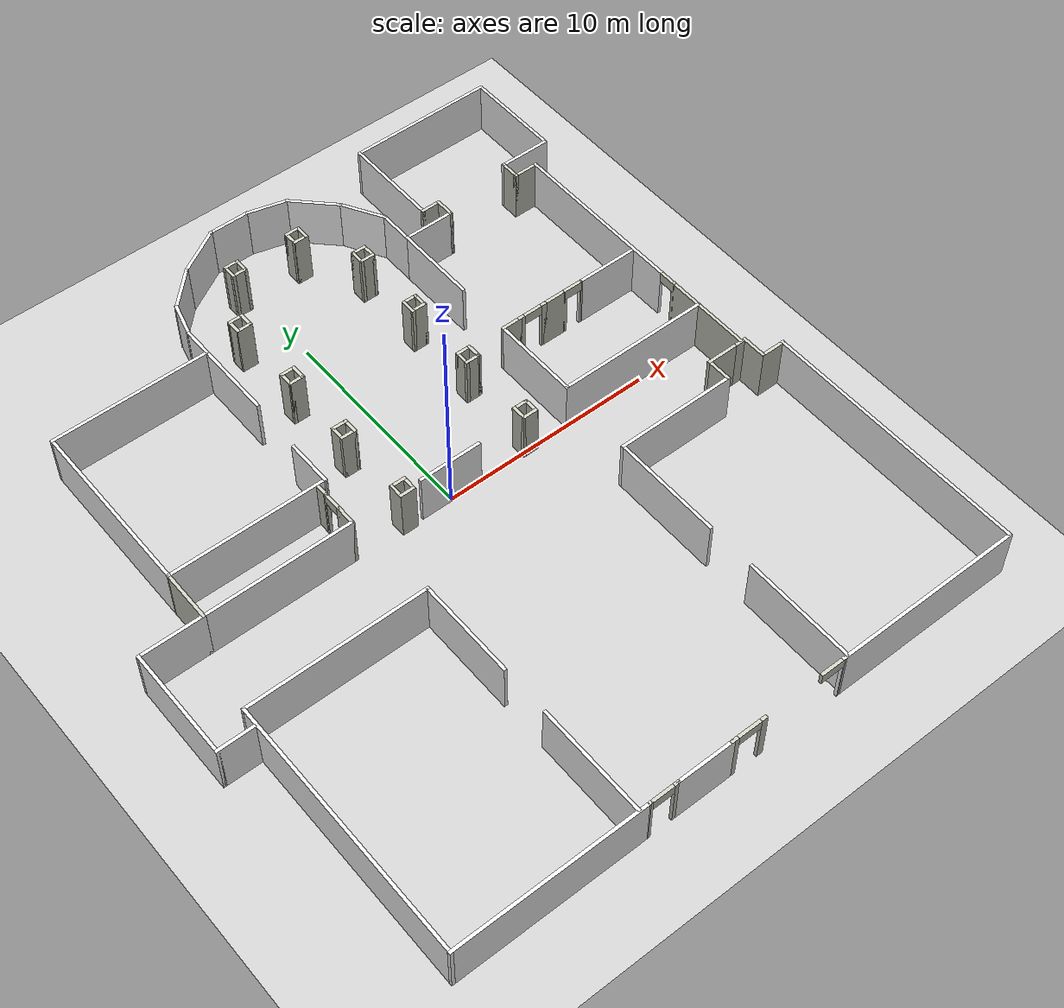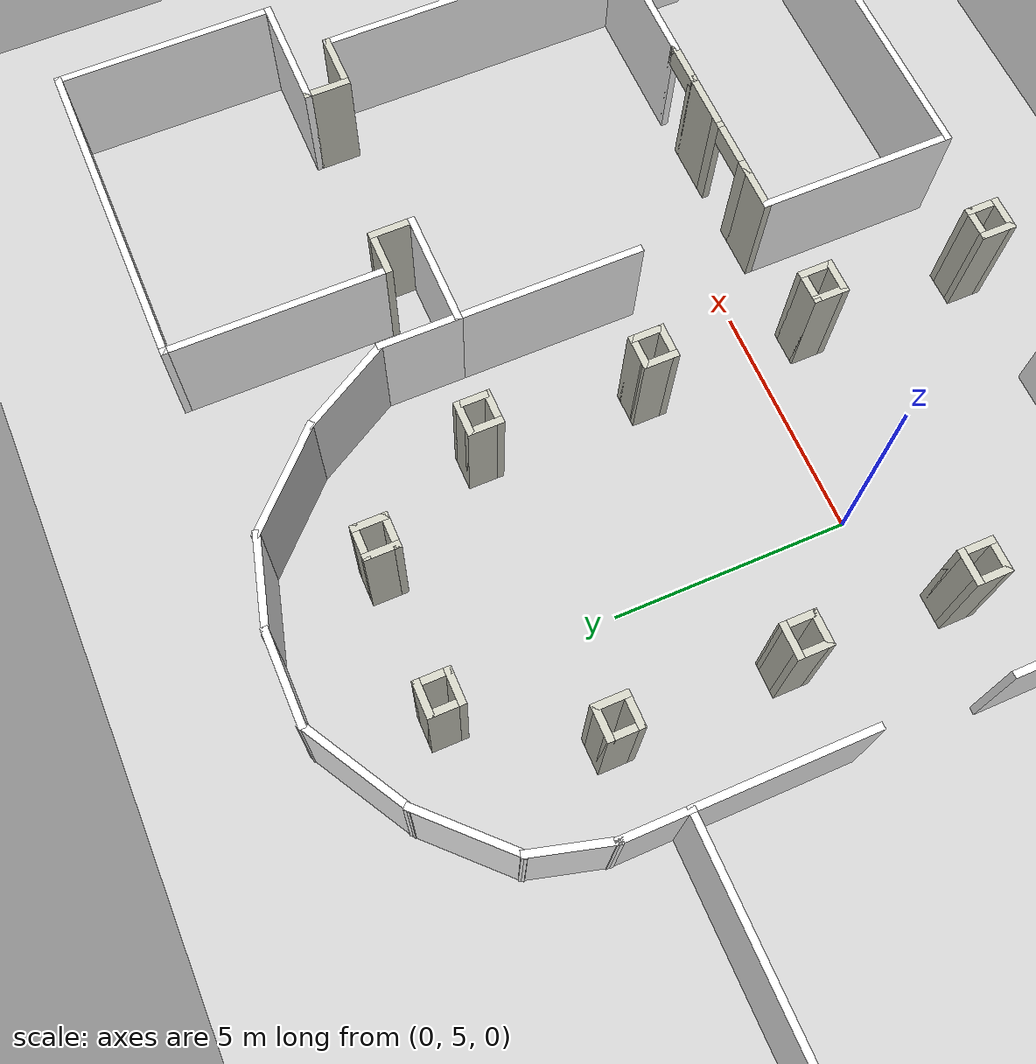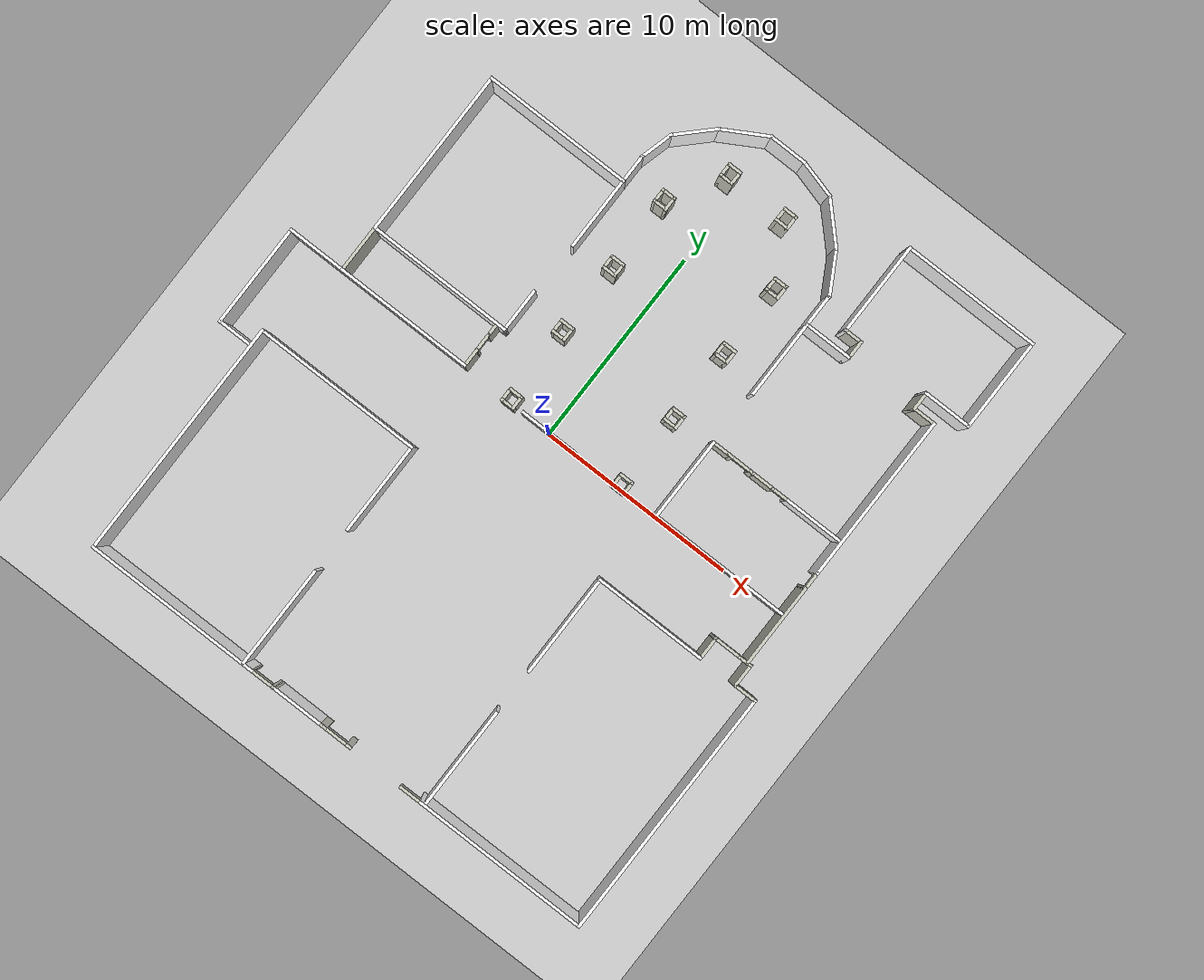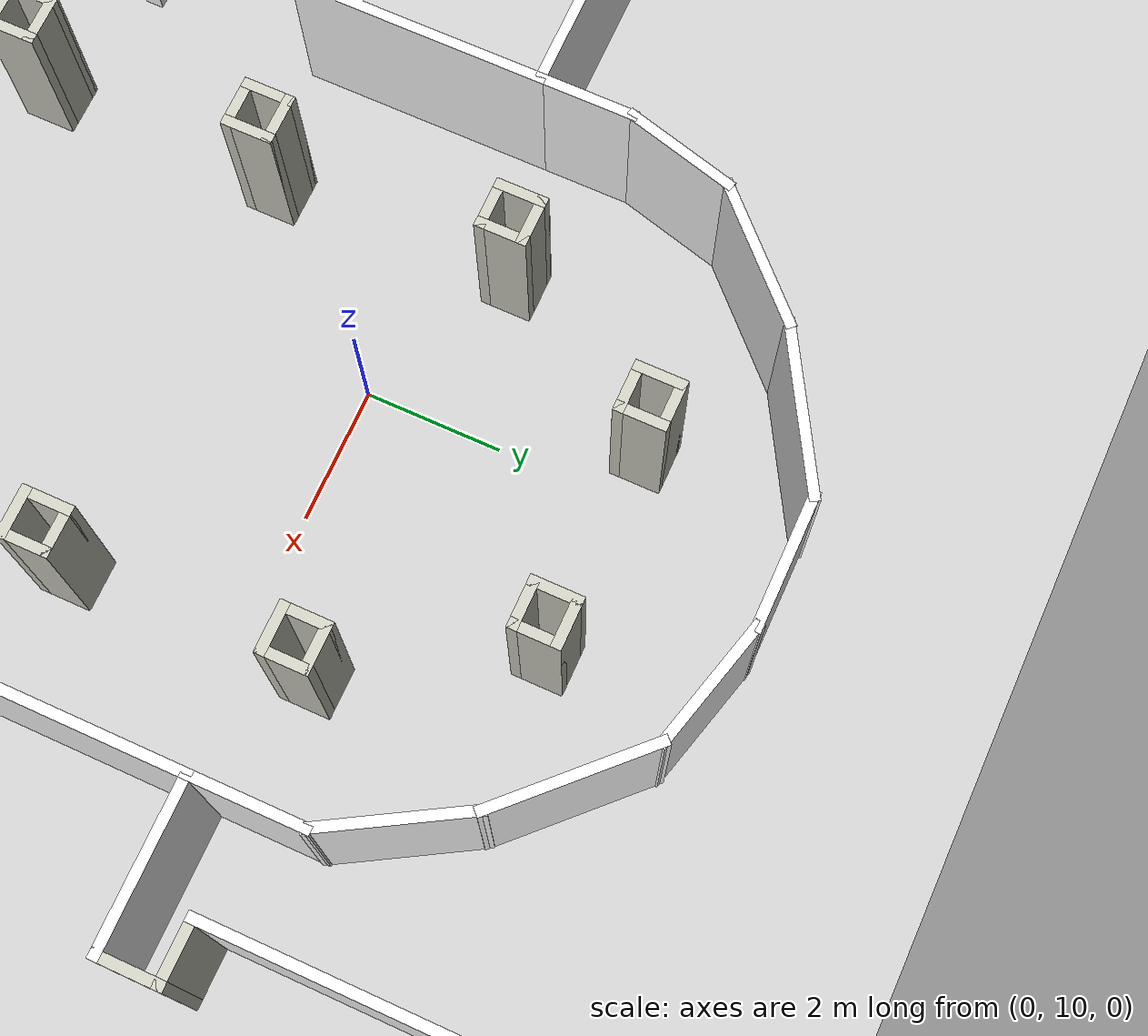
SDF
<sdf version="1.6">
 <world name="default">
  <model name="ground_plane">
   <static>1</static>
   <link name="link">
    <collision name="collision">
     <geometry><plane><normal>0 0 1</normal><size>100 100</size></plane></geometry>
     <surface><friction><ode><mu>100</mu><mu2>50</mu2></ode></friction></surface>
    </collision>
    <visual name="visual">
     <cast_shadows>0</cast_shadows>
     <geometry><plane><normal>0 0 1</normal><size>100 100</size></plane></geometry>
     <material>
      <script><uri>file://media/materials/scripts/gazebo.material</uri><name>Gazebo/Grey</name></script>
     </material>
    </visual>
   </link>
  </model>
  <light name="sun" type="directional">
   <pose>0 0 10 0 -0 0</pose>
   <diffuse>0.8 0.8 0.8 1</diffuse>
   <specular>0.1 0.1 0.1 1</specular>
   <attenuation>
    <range>1000</range>
    <constant>0.9</constant>
    <linear>0.01</linear>
    <quadratic>0.001</quadratic>
   </attenuation>
   <direction>-0.5 0.5 -1</direction>
  </light>
  <model name="museum">
   <link name="Wall_0">
    <collision name="Wall_0_Collision">
     <geometry><box><size>7.5 0.15 2.5</size></box></geometry>
     <pose>0 0 1.25 0 -0 0</pose>
    </collision>
    <visual name="Wall_0_Visual">
     <pose>0 0 1.25 0 -0 0</pose>
     <geometry><box><size>7.5 0.15 2.5</size></box></geometry>
     <material>
      <script><uri>file://media/materials/scripts/gazebo.material</uri><name>Gazebo/Image15</name></script>
      <ambient>1 1 1 1</ambient>
     </material>
    </visual>
    <pose>-7.91012 10.7458 0 0 -0 0</pose>
   </link>
   <link name="Wall_1">
    <collision name="Wall_1_Collision">
     <geometry><box><size>3.75 0.15 2.5</size></box></geometry>
     <pose>0 0 1.25 0 -0 0</pose>
    </collision>
    <visual name="Wall_1_Visual">
     <pose>0 0 1.25 0 -0 0</pose>
     <geometry><box><size>3.75 0.15 2.5</size></box></geometry>
     <material>
      <script><uri>file://media/materials/scripts/gazebo.material</uri><name>Gazebo/Image22</name></script>
      <ambient>1 1 1 1</ambient>
     </material>
    </visual>
    <pose>-4.23512 8.94576 0 0 0 -1.5708</pose>
   </link>
   <link name="Wall_10">
    <collision name="Wall_10_Collision">
     <geometry><box><size>1.5 0.15 2.5</size></box></geometry>
     <pose>0 0 1.25 0 -0 0</pose>
    </collision>
    <visual name="Wall_10_Visual">
     <pose>0 0 1.25 0 -0 0</pose>
     <geometry><box><size>1.5 0.15 2.5</size></box></geometry>
     <material>
      <script><uri>file://media/materials/scripts/gazebo.material</uri><name>Gazebo/Image31</name></script>
      <ambient>1 1 1 1</ambient>
     </material>
    </visual>
    <pose>-4.23512 11.4208 0 0 -0 1.5708</pose>
   </link>
   <link name="Wall_115">
    <collision name="Wall_115_Collision">
     <geometry><box><size>2.5 0.15 2.5</size></box></geometry>
     <pose>0 0 1.25 0 -0 0</pose>
    </collision>
    <visual name="Wall_115_Visual">
     <pose>0 0 1.25 0 -0 0</pose>
     <geometry><box><size>2.5 0.15 2.5</size></box></geometry>
     <material>
      <script><uri>file://media/materials/scripts/gazebo.material</uri><name>Gazebo/PaintedWall</name></script>
      <ambient>1 1 1 1</ambient>
     </material>
    </visual>
    <pose>-11.5851 1.22076 0 0 0 -1.5708</pose>
   </link>
   <link name="Wall_122">
    <collision name="Wall_122_Collision">
     <geometry><box><size>7 0.15 2.5</size></box></geometry>
     <pose>0 0 1.25 0 -0 0</pose>
    </collision>
    <visual name="Wall_122_Visual">
     <pose>0 0 1.25 0 -0 0</pose>
     <geometry><box><size>7 0.15 2.5</size></box></geometry>
     <material>
      <script><uri>file://media/materials/scripts/gazebo.material</uri><name>Gazebo/Image13</name></script>
      <ambient>1 1 1 1</ambient>
     </material>
    </visual>
    <pose>-8.16012 0.045757 0 0 -0 0</pose>
   </link>
   <link name="Wall_125">
    <collision name="Wall_125_Collision">
     <geometry><box><size>1 0.15 2.5</size></box></geometry>
     <pose>0 0 1.25 0 -0 0</pose>
    </collision>
    <visual name="Wall_125_Visual">
     <pose>0 0 1.25 0 -0 0</pose>
     <geometry><box><size>1 0.15 2.5</size></box></geometry>
     <material>
      <script><uri>file://media/materials/scripts/gazebo.material</uri><name>Gazebo/PaintedWall</name></script>
      <ambient>1 1 1 1</ambient>
     </material>
    </visual>
    <pose>-4.73512 0.470757 0 0 -0 1.5708</pose>
   </link>
   <link name="Wall_126">
    <pose>-4.73512 1.32076 0 0 -0 1.5708</pose>
    <visual name="Wall_126_Visual_0">
     <pose>-0.480087 0 1.25 0 -0 0</pose>
     <geometry><box><size>0.039827 0.15 2.5</size></box></geometry>
     <material>
      <script><uri>file://media/materials/scripts/gazebo.material</uri><name>Gazebo/PaintedWall</name></script>
      <ambient>1 1 1 1</ambient>
     </material>
    </visual>
    <collision name="Wall_126_Collision_0">
     <geometry><box><size>0.039827 0.15 2.5</size></box></geometry>
     <pose>-0.480087 0 1.25 0 -0 0</pose>
    </collision>
    <visual name="Wall_126_Visual_1">
     <pose>0.469913 0 1.25 0 -0 0</pose>
     <geometry><box><size>0.060173 0.15 2.5</size></box></geometry>
     <material>
      <script><uri>file://media/materials/scripts/gazebo.material</uri><name>Gazebo/PaintedWall</name></script>
      <ambient>1 1 1 1</ambient>
     </material>
    </visual>
    <collision name="Wall_126_Collision_1">
     <geometry><box><size>0.060173 0.15 2.5</size></box></geometry>
     <pose>0.469913 0 1.25 0 -0 0</pose>
    </collision>
    <visual name="Wall_126_Visual_2">
     <pose>-0.010173 0 2.25 0 -0 0</pose>
     <geometry><box><size>0.9 0.15 0.5</size></box></geometry>
     <material>
      <script><uri>file://media/materials/scripts/gazebo.material</uri><name>Gazebo/PaintedWall</name></script>
      <ambient>1 1 1 1</ambient>
     </material>
    </visual>
    <collision name="Wall_126_Collision_2">
     <geometry><box><size>0.9 0.15 0.5</size></box></geometry>
     <pose>-0.010173 0 2.25 0 -0 0</pose>
    </collision>
   </link>
   <link name="Wall_127">
    <collision name="Wall_127_Collision">
     <geometry><box><size>0.75 0.15 2.5</size></box></geometry>
     <pose>0 0 1.25 0 -0 0</pose>
    </collision>
    <visual name="Wall_127_Visual">
     <pose>0 0 1.25 0 -0 0</pose>
     <geometry><box><size>0.75 0.15 2.5</size></box></geometry>
     <material>
      <script><uri>file://media/materials/scripts/gazebo.material</uri><name>Gazebo/PaintedWall</name></script>
      <ambient>1 1 1 1</ambient>
     </material>
    </visual>
    <pose>-4.73512 2.04576 0 0 -0 1.5708</pose>
   </link>
   <link name="Wall_135">
    <collision name="Wall_135_Collision">
     <geometry><box><size>3 0.15 2.5</size></box></geometry>
     <pose>0 0 1.25 0 -0 0</pose>
    </collision>
    <visual name="Wall_135_Visual">
     <pose>0 0 1.25 0 -0 0</pose>
     <geometry><box><size>3 0.15 2.5</size></box></geometry>
     <material>
      <script><uri>file://media/materials/scripts/gazebo.material</uri><name>Gazebo/Image27</name></script>
      <ambient>1 1 1 1</ambient>
     </material>
    </visual>
    <pose>-13.0101 0.045757 0 0 -0 3.14159</pose>
   </link>
   <link name="Wall_139">
    <collision name="Wall_139_Collision">
     <geometry><box><size>5.25 0.15 2.5</size></box></geometry>
     <pose>0 0 1.25 0 -0 0</pose>
    </collision>
    <visual name="Wall_139_Visual">
     <pose>0 0 1.25 0 -0 0</pose>
     <geometry><box><size>5.25 0.15 2.5</size></box></geometry>
     <material>
      <script><uri>file://media/materials/scripts/gazebo.material</uri><name>Gazebo/Image14</name></script>
      <ambient>1 1 1 1</ambient>
     </material>
    </visual>
    <pose>-14.4351 -2.50424 0 0 0 -1.5708</pose>
   </link>
   <link name="Wall_141">
    <collision name="Wall_141_Collision">
     <geometry><box><size>1.75 0.15 2.5</size></box></geometry>
     <pose>0 0 1.25 0 -0 0</pose>
    </collision>
    <visual name="Wall_141_Visual">
     <pose>0 0 1.25 0 -0 0</pose>
     <geometry><box><size>1.75 0.15 2.5</size></box></geometry>
     <material>
      <script><uri>file://media/materials/scripts/gazebo.material</uri><name>Gazebo/Image30</name></script>
      <ambient>1 1 1 1</ambient>
     </material>
    </visual>
    <pose>-13.6351 -5.05424 0 0 -0 0</pose>
   </link>
   <link name="Wall_146">
    <pose>13.1477 1.96699 0 0 0 -1.5708</pose>
    <visual name="Wall_146_Visual_0">
     <pose>-0.441517 0 1.25 0 -0 0</pose>
     <geometry><box><size>0.116967 0.15 2.5</size></box></geometry>
     <material>
      <script><uri>file://media/materials/scripts/gazebo.material</uri><name>Gazebo/PaintedWall</name></script>
      <ambient>1 1 1 1</ambient>
     </material>
    </visual>
    <collision name="Wall_146_Collision_0">
     <geometry><box><size>0.116967 0.15 2.5</size></box></geometry>
     <pose>-0.441517 0 1.25 0 -0 0</pose>
    </collision>
    <visual name="Wall_146_Visual_1">
     <pose>0.488483 0 1.25 0 -0 0</pose>
     <geometry><box><size>0.023033 0.15 2.5</size></box></geometry>
     <material>
      <script><uri>file://media/materials/scripts/gazebo.material</uri><name>Gazebo/PaintedWall</name></script>
      <ambient>1 1 1 1</ambient>
     </material>
    </visual>
    <collision name="Wall_146_Collision_1">
     <geometry><box><size>0.023033 0.15 2.5</size></box></geometry>
     <pose>0.488483 0 1.25 0 -0 0</pose>
    </collision>
    <visual name="Wall_146_Visual_2">
     <pose>0.046967 0 2.25 0 -0 0</pose>
     <geometry><box><size>0.86 0.15 0.5</size></box></geometry>
     <material>
      <script><uri>file://media/materials/scripts/gazebo.material</uri><name>Gazebo/PaintedWall</name></script>
      <ambient>1 1 1 1</ambient>
     </material>
    </visual>
    <collision name="Wall_146_Collision_2">
     <geometry><box><size>0.86 0.15 0.5</size></box></geometry>
     <pose>0.046967 0 2.25 0 -0 0</pose>
    </collision>
   </link>
   <link name="Wall_15">
    <collision name="Wall_15_Collision">
     <geometry><box><size>1.75 0.15 2.5</size></box></geometry>
     <pose>0 0 1.25 0 -0 0</pose>
    </collision>
    <visual name="Wall_15_Visual">
     <pose>0 0 1.25 0 -0 0</pose>
     <geometry><box><size>1.75 0.15 2.5</size></box></geometry>
     <material>
      <script><uri>file://media/materials/scripts/gazebo.material</uri><name>Gazebo/Image32</name></script>
      <ambient>1 1 1 1</ambient>
     </material>
    </visual>
    <pose>-4.02806 12.8685 0 0 -0 1.309</pose>
   </link>
   <link name="Wall_16">
    <collision name="Wall_16_Collision">
     <geometry><box><size>2.25 0.15 2.5</size></box></geometry>
     <pose>0 0 1.25 0 -0 0</pose>
    </collision>
    <visual name="Wall_16_Visual">
     <pose>0 0 1.25 0 -0 0</pose>
     <geometry><box><size>2.25 0.15 2.5</size></box></geometry>
     <material>
      <script><uri>file://media/materials/scripts/gazebo.material</uri><name>Gazebo/Image33</name></script>
      <ambient>1 1 1 1</ambient>
     </material>
    </visual>
    <pose>-3.07855 14.3837 0 0 -0 0.785398</pose>
   </link>
   <link name="Wall_160">
    <collision name="Wall_160_Collision">
     <geometry><box><size>4.25 0.15 2.5</size></box></geometry>
     <pose>0 0 1.25 0 -0 0</pose>
    </collision>
    <visual name="Wall_160_Visual">
     <pose>0 0 1.25 0 -0 0</pose>
     <geometry><box><size>4.25 0.15 2.5</size></box></geometry>
     <material>
      <script><uri>file://media/materials/scripts/gazebo.material</uri><name>Gazebo/PaintedWall</name></script>
      <ambient>1 1 1 1</ambient>
     </material>
    </visual>
    <pose>13.1477 -0.508007 0 0 0 -1.5708</pose>
   </link>
   <link name="Wall_166">
    <collision name="Wall_166_Collision">
     <geometry><box><size>5.25 0.15 2.5</size></box></geometry>
     <pose>0 0 1.25 0 -0 0</pose>
    </collision>
    <visual name="Wall_166_Visual">
     <pose>0 0 1.25 0 -0 0</pose>
     <geometry><box><size>5.25 0.15 2.5</size></box></geometry>
     <material>
      <script><uri>file://media/materials/scripts/gazebo.material</uri><name>Gazebo/Image2</name></script>
      <ambient>1 1 1 1</ambient>
     </material>
    </visual>
    <pose>-4.36045 -13.7284 0 0 0 -1.5708</pose>
   </link>
   <link name="Wall_17">
    <collision name="Wall_17_Collision">
     <geometry><box><size>2.5 0.15 2.5</size></box></geometry>
     <pose>0 0 1.25 0 -0 0</pose>
    </collision>
    <visual name="Wall_17_Visual">
     <pose>0 0 1.25 0 -0 0</pose>
     <geometry><box><size>2.5 0.15 2.5</size></box></geometry>
     <material>
      <script><uri>file://media/materials/scripts/gazebo.material</uri><name>Gazebo/Image34</name></script>
      <ambient>1 1 1 1</ambient>
     </material>
    </visual>
    <pose>-1.3185 15.7137 0 0 -0 0.523599</pose>
   </link>
   <link name="Wall_170">
    <collision name="Wall_170_Collision">
     <geometry><box><size>3 0.15 2.5</size></box></geometry>
     <pose>0 0 1.25 0 -0 0</pose>
    </collision>
    <visual name="Wall_170_Visual">
     <pose>0 0 1.25 0 -0 0</pose>
     <geometry><box><size>3 0.15 2.5</size></box></geometry>
     <material>
      <script><uri>file://media/materials/scripts/gazebo.material</uri><name>Gazebo/Image25</name></script>
      <ambient>1 1 1 1</ambient>
     </material>
    </visual>
   </link>
   <link name="Wall_18">
    <collision name="Wall_18_Collision">
     <geometry><box><size>2 0.15 2.5</size></box></geometry>
     <pose>0 0 1.25 0 -0 0</pose>
    </collision>
    <visual name="Wall_18_Visual">
     <pose>0 0 1.25 0 -0 0</pose>
     <geometry><box><size>2 0.15 2.5</size></box></geometry>
     <material>
      <script><uri>file://media/materials/scripts/gazebo.material</uri><name>Gazebo/Image35</name></script>
      <ambient>1 1 1 1</ambient>
     </material>
    </visual>
    <pose>0.624076 16.3012 0 0 -0 0</pose>
   </link>
   <link name="Wall_184">
    <pose>7.52862 4.1183 0 0 -0 0</pose>
    <visual name="Wall_184_Visual_0">
     <pose>-0.586918 0 1.25 0 -0 0</pose>
     <geometry><box><size>0.326163 0.15 2.5</size></box></geometry>
     <material>
      <script><uri>file://media/materials/scripts/gazebo.material</uri><name>Gazebo/PaintedWall</name></script>
      <ambient>1 1 1 1</ambient>
     </material>
    </visual>
    <collision name="Wall_184_Collision_0">
     <geometry><box><size>0.326163 0.15 2.5</size></box></geometry>
     <pose>-0.586918 0 1.25 0 -0 0</pose>
    </collision>
    <visual name="Wall_184_Visual_1">
     <pose>0.613082 0 1.25 0 -0 0</pose>
     <geometry><box><size>0.273837 0.15 2.5</size></box></geometry>
     <material>
      <script><uri>file://media/materials/scripts/gazebo.material</uri><name>Gazebo/PaintedWall</name></script>
      <ambient>1 1 1 1</ambient>
     </material>
    </visual>
    <collision name="Wall_184_Collision_1">
     <geometry><box><size>0.273837 0.15 2.5</size></box></geometry>
     <pose>0.613082 0 1.25 0 -0 0</pose>
    </collision>
    <visual name="Wall_184_Visual_2">
     <pose>0.026163 0 2.25 0 -0 0</pose>
     <geometry><box><size>0.9 0.15 0.5</size></box></geometry>
     <material>
      <script><uri>file://media/materials/scripts/gazebo.material</uri><name>Gazebo/PaintedWall</name></script>
      <ambient>1 1 1 1</ambient>
     </material>
    </visual>
    <collision name="Wall_184_Collision_2">
     <geometry><box><size>0.9 0.15 0.5</size></box></geometry>
     <pose>0.026163 0 2.25 0 -0 0</pose>
    </collision>
   </link>
   <link name="Wall_185">
    <collision name="Wall_185_Collision">
     <geometry><box><size>1.25 0.15 2.5</size></box></geometry>
     <pose>0 0 1.25 0 -0 0</pose>
    </collision>
    <visual name="Wall_185_Visual">
     <pose>0 0 1.25 0 -0 0</pose>
     <geometry><box><size>1.25 0.15 2.5</size></box></geometry>
     <material>
      <script><uri>file://media/materials/scripts/gazebo.material</uri><name>Gazebo/PaintedWall</name></script>
      <ambient>1 1 1 1</ambient>
     </material>
    </visual>
    <pose>8.75362 4.1183 0 0 -0 0</pose>
   </link>
   <link name="Wall_186">
    <pose>9.72862 4.1183 0 0 -0 0</pose>
    <visual name="Wall_186_Visual_0">
     <pose>-0.486669 0 1.25 0 -0 0</pose>
     <geometry><box><size>0.026662 0.15 2.5</size></box></geometry>
     <material>
      <script><uri>file://media/materials/scripts/gazebo.material</uri><name>Gazebo/PaintedWall</name></script>
      <ambient>1 1 1 1</ambient>
     </material>
    </visual>
    <collision name="Wall_186_Collision_0">
     <geometry><box><size>0.026662 0.15 2.5</size></box></geometry>
     <pose>-0.486669 0 1.25 0 -0 0</pose>
    </collision>
    <visual name="Wall_186_Visual_1">
     <pose>0.463331 0 1.25 0 -0 0</pose>
     <geometry><box><size>0.073338 0.15 2.5</size></box></geometry>
     <material>
      <script><uri>file://media/materials/scripts/gazebo.material</uri><name>Gazebo/PaintedWall</name></script>
      <ambient>1 1 1 1</ambient>
     </material>
    </visual>
    <collision name="Wall_186_Collision_1">
     <geometry><box><size>0.073338 0.15 2.5</size></box></geometry>
     <pose>0.463331 0 1.25 0 -0 0</pose>
    </collision>
    <visual name="Wall_186_Visual_2">
     <pose>-0.023338 0 2.25 0 -0 0</pose>
     <geometry><box><size>0.9 0.15 0.5</size></box></geometry>
     <material>
      <script><uri>file://media/materials/scripts/gazebo.material</uri><name>Gazebo/PaintedWall</name></script>
      <ambient>1 1 1 1</ambient>
     </material>
    </visual>
    <collision name="Wall_186_Collision_2">
     <geometry><box><size>0.9 0.15 0.5</size></box></geometry>
     <pose>-0.023338 0 2.25 0 -0 0</pose>
    </collision>
   </link>
   <link name="Wall_187">
    <collision name="Wall_187_Collision">
     <geometry><box><size>3 0.15 2.5</size></box></geometry>
     <pose>0 0 1.25 0 -0 0</pose>
    </collision>
    <visual name="Wall_187_Visual">
     <pose>0 0 1.25 0 -0 0</pose>
     <geometry><box><size>3 0.15 2.5</size></box></geometry>
     <material>
      <script><uri>file://media/materials/scripts/gazebo.material</uri><name>Gazebo/Image40</name></script>
      <ambient>1 1 1 1</ambient>
     </material>
    </visual>
    <pose>11.5786 4.1183 0 0 -0 0</pose>
   </link>
   <link name="Wall_189">
    <collision name="Wall_189_Collision">
     <geometry><box><size>4 0.15 2.5</size></box></geometry>
     <pose>0 0 1.25 0 -0 0</pose>
    </collision>
    <visual name="Wall_189_Visual">
     <pose>0 0 1.25 0 -0 0</pose>
     <geometry><box><size>4 0.15 2.5</size></box></geometry>
     <material>
      <script><uri>file://media/materials/scripts/gazebo.material</uri><name>Gazebo/Image21</name></script>
      <ambient>1 1 1 1</ambient>
     </material>
    </visual>
    <pose>6.04774 8.81699 0 0 0 -1.5708</pose>
   </link>
   <link name="Wall_19">
    <collision name="Wall_19_Collision">
     <geometry><box><size>2 0.15 2.5</size></box></geometry>
     <pose>0 0 1.25 0 -0 0</pose>
    </collision>
    <visual name="Wall_19_Visual">
     <pose>0 0 1.25 0 -0 0</pose>
     <geometry><box><size>2 0.15 2.5</size></box></geometry>
     <material>
      <script><uri>file://media/materials/scripts/gazebo.material</uri><name>Gazebo/Image36</name></script>
      <ambient>1 1 1 1</ambient>
     </material>
    </visual>
    <pose>2.44256 16.0618 0 0 0 -0.261799</pose>
   </link>
   <link name="Wall_192">
    <collision name="Wall_192_Collision">
     <geometry><box><size>0.75 0.15 2.5</size></box></geometry>
     <pose>0 0 1.25 0 -0 0</pose>
    </collision>
    <visual name="Wall_192_Visual">
     <pose>0 0 1.25 0 -0 0</pose>
     <geometry><box><size>0.75 0.15 2.5</size></box></geometry>
     <material>
      <script><uri>file://media/materials/scripts/gazebo.material</uri><name>Gazebo/PaintedWall</name></script>
      <ambient>1 1 1 1</ambient>
     </material>
    </visual>
    <pose>-2.20621 0.469078 0 0 -0 0</pose>
   </link>
   <link name="Wall_193">
    <collision name="Wall_193_Collision">
     <geometry><box><size>0.75 0.15 2.5</size></box></geometry>
     <pose>0 0 1.25 0 -0 0</pose>
    </collision>
    <visual name="Wall_193_Visual">
     <pose>0 0 1.25 0 -0 0</pose>
     <geometry><box><size>0.75 0.15 2.5</size></box></geometry>
     <material>
      <script><uri>file://media/materials/scripts/gazebo.material</uri><name>Gazebo/PaintedWall</name></script>
      <ambient>1 1 1 1</ambient>
     </material>
    </visual>
    <pose>-1.90621 0.169078 0 0 0 -1.5708</pose>
   </link>
   <link name="Wall_194">
    <collision name="Wall_194_Collision">
     <geometry><box><size>0.75 0.15 2.5</size></box></geometry>
     <pose>0 0 1.25 0 -0 0</pose>
    </collision>
    <visual name="Wall_194_Visual">
     <pose>0 0 1.25 0 -0 0</pose>
     <geometry><box><size>0.75 0.15 2.5</size></box></geometry>
     <material>
      <script><uri>file://media/materials/scripts/gazebo.material</uri><name>Gazebo/PaintedWall</name></script>
      <ambient>1 1 1 1</ambient>
     </material>
    </visual>
    <pose>-2.20621 -0.130922 0 0 -0 3.14159</pose>
   </link>
   <link name="Wall_195">
    <collision name="Wall_195_Collision">
     <geometry><box><size>0.75 0.15 2.5</size></box></geometry>
     <pose>0 0 1.25 0 -0 0</pose>
    </collision>
    <visual name="Wall_195_Visual">
     <pose>0 0 1.25 0 -0 0</pose>
     <geometry><box><size>0.75 0.15 2.5</size></box></geometry>
     <material>
      <script><uri>file://media/materials/scripts/gazebo.material</uri><name>Gazebo/PaintedWall</name></script>
      <ambient>1 1 1 1</ambient>
     </material>
    </visual>
    <pose>-2.50622 0.169078 0 0 -0 1.5708</pose>
   </link>
   <link name="Wall_197">
    <collision name="Wall_197_Collision">
     <geometry><box><size>0.75 0.15 2.5</size></box></geometry>
     <pose>0 0 1.25 0 -0 0</pose>
    </collision>
    <visual name="Wall_197_Visual">
     <pose>0 0 1.25 0 -0 0</pose>
     <geometry><box><size>0.75 0.15 2.5</size></box></geometry>
     <material>
      <script><uri>file://media/materials/scripts/gazebo.material</uri><name>Gazebo/PaintedWall</name></script>
      <ambient>1 1 1 1</ambient>
     </material>
    </visual>
    <pose>3.9677 0.495165 0 0 -0 0</pose>
   </link>
   <link name="Wall_198">
    <collision name="Wall_198_Collision">
     <geometry><box><size>0.75 0.15 2.5</size></box></geometry>
     <pose>0 0 1.25 0 -0 0</pose>
    </collision>
    <visual name="Wall_198_Visual">
     <pose>0 0 1.25 0 -0 0</pose>
     <geometry><box><size>0.75 0.15 2.5</size></box></geometry>
     <material>
      <script><uri>file://media/materials/scripts/gazebo.material</uri><name>Gazebo/PaintedWall</name></script>
      <ambient>1 1 1 1</ambient>
     </material>
    </visual>
    <pose>4.2677 0.195165 0 0 0 -1.5708</pose>
   </link>
   <link name="Wall_199">
    <collision name="Wall_199_Collision">
     <geometry><box><size>0.75 0.15 2.5</size></box></geometry>
     <pose>0 0 1.25 0 -0 0</pose>
    </collision>
    <visual name="Wall_199_Visual">
     <pose>0 0 1.25 0 -0 0</pose>
     <geometry><box><size>0.75 0.15 2.5</size></box></geometry>
     <material>
      <script><uri>file://media/materials/scripts/gazebo.material</uri><name>Gazebo/PaintedWall</name></script>
      <ambient>1 1 1 1</ambient>
     </material>
    </visual>
    <pose>3.9677 -0.104835 0 0 -0 3.14159</pose>
   </link>
   <link name="Wall_20">
    <collision name="Wall_20_Collision">
     <geometry><box><size>2.5 0.15 2.5</size></box></geometry>
     <pose>0 0 1.25 0 -0 0</pose>
    </collision>
    <visual name="Wall_20_Visual">
     <pose>0 0 1.25 0 -0 0</pose>
     <geometry><box><size>2.5 0.15 2.5</size></box></geometry>
     <material>
      <script><uri>file://media/materials/scripts/gazebo.material</uri><name>Gazebo/Image37</name></script>
      <ambient>1 1 1 1</ambient>
     </material>
    </visual>
    <pose>4.16689 14.9915 0 0 0 -0.785398</pose>
   </link>
   <link name="Wall_200">
    <collision name="Wall_200_Collision">
     <geometry><box><size>0.75 0.15 2.5</size></box></geometry>
     <pose>0 0 1.25 0 -0 0</pose>
    </collision>
    <visual name="Wall_200_Visual">
     <pose>0 0 1.25 0 -0 0</pose>
     <geometry><box><size>0.75 0.15 2.5</size></box></geometry>
     <material>
      <script><uri>file://media/materials/scripts/gazebo.material</uri><name>Gazebo/PaintedWall</name></script>
      <ambient>1 1 1 1</ambient>
     </material>
    </visual>
    <pose>3.6677 0.195165 0 0 -0 1.5708</pose>
   </link>
   <link name="Wall_202">
    <collision name="Wall_202_Collision">
     <geometry><box><size>0.75 0.15 2.5</size></box></geometry>
     <pose>0 0 1.25 0 -0 0</pose>
    </collision>
    <visual name="Wall_202_Visual">
     <pose>0 0 1.25 0 -0 0</pose>
     <geometry><box><size>0.75 0.15 2.5</size></box></geometry>
     <material>
      <script><uri>file://media/materials/scripts/gazebo.material</uri><name>Gazebo/PaintedWall</name></script>
      <ambient>1 1 1 1</ambient>
     </material>
    </visual>
    <pose>-2.28448 4.2343 0 0 -0 0</pose>
   </link>
   <link name="Wall_203">
    <collision name="Wall_203_Collision">
     <geometry><box><size>0.75 0.15 2.5</size></box></geometry>
     <pose>0 0 1.25 0 -0 0</pose>
    </collision>
    <visual name="Wall_203_Visual">
     <pose>0 0 1.25 0 -0 0</pose>
     <geometry><box><size>0.75 0.15 2.5</size></box></geometry>
     <material>
      <script><uri>file://media/materials/scripts/gazebo.material</uri><name>Gazebo/PaintedWall</name></script>
      <ambient>1 1 1 1</ambient>
     </material>
    </visual>
    <pose>-1.98447 3.9343 0 0 0 -1.5708</pose>
   </link>
   <link name="Wall_204">
    <collision name="Wall_204_Collision">
     <geometry><box><size>0.75 0.15 2.5</size></box></geometry>
     <pose>0 0 1.25 0 -0 0</pose>
    </collision>
    <visual name="Wall_204_Visual">
     <pose>0 0 1.25 0 -0 0</pose>
     <geometry><box><size>0.75 0.15 2.5</size></box></geometry>
     <material>
      <script><uri>file://media/materials/scripts/gazebo.material</uri><name>Gazebo/PaintedWall</name></script>
      <ambient>1 1 1 1</ambient>
     </material>
    </visual>
    <pose>-2.28448 3.6343 0 0 -0 3.14159</pose>
   </link>
   <link name="Wall_205">
    <collision name="Wall_205_Collision">
     <geometry><box><size>0.75 0.15 2.5</size></box></geometry>
     <pose>0 0 1.25 0 -0 0</pose>
    </collision>
    <visual name="Wall_205_Visual">
     <pose>0 0 1.25 0 -0 0</pose>
     <geometry><box><size>0.75 0.15 2.5</size></box></geometry>
     <material>
      <script><uri>file://media/materials/scripts/gazebo.material</uri><name>Gazebo/PaintedWall</name></script>
      <ambient>1 1 1 1</ambient>
     </material>
    </visual>
    <pose>-2.58448 3.9343 0 0 -0 1.5708</pose>
   </link>
   <link name="Wall_207">
    <collision name="Wall_207_Collision">
     <geometry><box><size>0.75 0.15 2.5</size></box></geometry>
     <pose>0 0 1.25 0 -0 0</pose>
    </collision>
    <visual name="Wall_207_Visual">
     <pose>0 0 1.25 0 -0 0</pose>
     <geometry><box><size>0.75 0.15 2.5</size></box></geometry>
     <material>
      <script><uri>file://media/materials/scripts/gazebo.material</uri><name>Gazebo/PaintedWall</name></script>
      <ambient>1 1 1 1</ambient>
     </material>
    </visual>
    <pose>3.98509 4.20821 0 0 -0 0</pose>
   </link>
   <link name="Wall_208">
    <collision name="Wall_208_Collision">
     <geometry><box><size>0.75 0.15 2.5</size></box></geometry>
     <pose>0 0 1.25 0 -0 0</pose>
    </collision>
    <visual name="Wall_208_Visual">
     <pose>0 0 1.25 0 -0 0</pose>
     <geometry><box><size>0.75 0.15 2.5</size></box></geometry>
     <material>
      <script><uri>file://media/materials/scripts/gazebo.material</uri><name>Gazebo/PaintedWall</name></script>
      <ambient>1 1 1 1</ambient>
     </material>
    </visual>
    <pose>4.28509 3.90821 0 0 0 -1.5708</pose>
   </link>
   <link name="Wall_209">
    <collision name="Wall_209_Collision">
     <geometry><box><size>0.75 0.15 2.5</size></box></geometry>
     <pose>0 0 1.25 0 -0 0</pose>
    </collision>
    <visual name="Wall_209_Visual">
     <pose>0 0 1.25 0 -0 0</pose>
     <geometry><box><size>0.75 0.15 2.5</size></box></geometry>
     <material>
      <script><uri>file://media/materials/scripts/gazebo.material</uri><name>Gazebo/PaintedWall</name></script>
      <ambient>1 1 1 1</ambient>
     </material>
    </visual>
    <pose>3.98509 3.60821 0 0 -0 3.14159</pose>
   </link>
   <link name="Wall_21">
    <collision name="Wall_21_Collision">
     <geometry><box><size>2.25 0.15 2.5</size></box></geometry>
     <pose>0 0 1.25 0 -0 0</pose>
    </collision>
    <visual name="Wall_21_Visual">
     <pose>0 0 1.25 0 -0 0</pose>
     <geometry><box><size>2.25 0.15 2.5</size></box></geometry>
     <material>
      <script><uri>file://media/materials/scripts/gazebo.material</uri><name>Gazebo/Image38</name></script>
      <ambient>1 1 1 1</ambient>
     </material>
    </visual>
    <pose>5.52274 13.2513 0 0 0 -1.0472</pose>
   </link>
   <link name="Wall_210">
    <collision name="Wall_210_Collision">
     <geometry><box><size>0.75 0.15 2.5</size></box></geometry>
     <pose>0 0 1.25 0 -0 0</pose>
    </collision>
    <visual name="Wall_210_Visual">
     <pose>0 0 1.25 0 -0 0</pose>
     <geometry><box><size>0.75 0.15 2.5</size></box></geometry>
     <material>
      <script><uri>file://media/materials/scripts/gazebo.material</uri><name>Gazebo/PaintedWall</name></script>
      <ambient>1 1 1 1</ambient>
     </material>
    </visual>
    <pose>3.68509 3.90821 0 0 -0 1.5708</pose>
   </link>
   <link name="Wall_212">
    <collision name="Wall_212_Collision">
     <geometry><box><size>0.75 0.15 2.5</size></box></geometry>
     <pose>0 0 1.25 0 -0 0</pose>
    </collision>
    <visual name="Wall_212_Visual">
     <pose>0 0 1.25 0 -0 0</pose>
     <geometry><box><size>0.75 0.15 2.5</size></box></geometry>
     <material>
      <script><uri>file://media/materials/scripts/gazebo.material</uri><name>Gazebo/PaintedWall</name></script>
      <ambient>1 1 1 1</ambient>
     </material>
    </visual>
    <pose>-2.25839 7.8256 0 0 -0 0</pose>
   </link>
   <link name="Wall_213">
    <collision name="Wall_213_Collision">
     <geometry><box><size>0.75 0.15 2.5</size></box></geometry>
     <pose>0 0 1.25 0 -0 0</pose>
    </collision>
    <visual name="Wall_213_Visual">
     <pose>0 0 1.25 0 -0 0</pose>
     <geometry><box><size>0.75 0.15 2.5</size></box></geometry>
     <material>
      <script><uri>file://media/materials/scripts/gazebo.material</uri><name>Gazebo/PaintedWall</name></script>
      <ambient>1 1 1 1</ambient>
     </material>
    </visual>
    <pose>-1.95839 7.5256 0 0 0 -1.5708</pose>
   </link>
   <link name="Wall_214">
    <collision name="Wall_214_Collision">
     <geometry><box><size>0.75 0.15 2.5</size></box></geometry>
     <pose>0 0 1.25 0 -0 0</pose>
    </collision>
    <visual name="Wall_214_Visual">
     <pose>0 0 1.25 0 -0 0</pose>
     <geometry><box><size>0.75 0.15 2.5</size></box></geometry>
     <material>
      <script><uri>file://media/materials/scripts/gazebo.material</uri><name>Gazebo/PaintedWall</name></script>
      <ambient>1 1 1 1</ambient>
     </material>
    </visual>
    <pose>-2.25839 7.2256 0 0 -0 3.14159</pose>
   </link>
   <link name="Wall_215">
    <collision name="Wall_215_Collision">
     <geometry><box><size>0.75 0.15 2.5</size></box></geometry>
     <pose>0 0 1.25 0 -0 0</pose>
    </collision>
    <visual name="Wall_215_Visual">
     <pose>0 0 1.25 0 -0 0</pose>
     <geometry><box><size>0.75 0.15 2.5</size></box></geometry>
     <material>
      <script><uri>file://media/materials/scripts/gazebo.material</uri><name>Gazebo/PaintedWall</name></script>
      <ambient>1 1 1 1</ambient>
     </material>
    </visual>
    <pose>-2.55839 7.5256 0 0 -0 1.5708</pose>
   </link>
   <link name="Wall_217">
    <collision name="Wall_217_Collision">
     <geometry><box><size>0.75 0.15 2.5</size></box></geometry>
     <pose>0 0 1.25 0 -0 0</pose>
    </collision>
    <visual name="Wall_217_Visual">
     <pose>0 0 1.25 0 -0 0</pose>
     <geometry><box><size>0.75 0.15 2.5</size></box></geometry>
     <material>
      <script><uri>file://media/materials/scripts/gazebo.material</uri><name>Gazebo/PaintedWall</name></script>
      <ambient>1 1 1 1</ambient>
     </material>
    </visual>
    <pose>3.98509 7.85169 0 0 -0 0</pose>
   </link>
   <link name="Wall_218">
    <collision name="Wall_218_Collision">
     <geometry><box><size>0.75 0.15 2.5</size></box></geometry>
     <pose>0 0 1.25 0 -0 0</pose>
    </collision>
    <visual name="Wall_218_Visual">
     <pose>0 0 1.25 0 -0 0</pose>
     <geometry><box><size>0.75 0.15 2.5</size></box></geometry>
     <material>
      <script><uri>file://media/materials/scripts/gazebo.material</uri><name>Gazebo/PaintedWall</name></script>
      <ambient>1 1 1 1</ambient>
     </material>
    </visual>
    <pose>4.28509 7.55169 0 0 0 -1.5708</pose>
   </link>
   <link name="Wall_219">
    <collision name="Wall_219_Collision">
     <geometry><box><size>0.75 0.15 2.5</size></box></geometry>
     <pose>0 0 1.25 0 -0 0</pose>
    </collision>
    <visual name="Wall_219_Visual">
     <pose>0 0 1.25 0 -0 0</pose>
     <geometry><box><size>0.75 0.15 2.5</size></box></geometry>
     <material>
      <script><uri>file://media/materials/scripts/gazebo.material</uri><name>Gazebo/PaintedWall</name></script>
      <ambient>1 1 1 1</ambient>
     </material>
    </visual>
    <pose>3.98509 7.25169 0 0 -0 3.14159</pose>
   </link>
   <link name="Wall_22">
    <collision name="Wall_22_Collision">
     <geometry><box><size>1.75 0.15 2.5</size></box></geometry>
     <pose>0 0 1.25 0 -0 0</pose>
    </collision>
    <visual name="Wall_22_Visual">
     <pose>0 0 1.25 0 -0 0</pose>
     <geometry><box><size>1.75 0.15 2.5</size></box></geometry>
     <material>
      <script><uri>file://media/materials/scripts/gazebo.material</uri><name>Gazebo/Image39</name></script>
      <ambient>1 1 1 1</ambient>
     </material>
    </visual>
    <pose>6.04774 11.542 0 0 0 -1.5708</pose>
   </link>
   <link name="Wall_220">
    <collision name="Wall_220_Collision">
     <geometry><box><size>0.75 0.15 2.5</size></box></geometry>
     <pose>0 0 1.25 0 -0 0</pose>
    </collision>
    <visual name="Wall_220_Visual">
     <pose>0 0 1.25 0 -0 0</pose>
     <geometry><box><size>0.75 0.15 2.5</size></box></geometry>
     <material>
      <script><uri>file://media/materials/scripts/gazebo.material</uri><name>Gazebo/PaintedWall</name></script>
      <ambient>1 1 1 1</ambient>
     </material>
    </visual>
    <pose>3.68509 7.55169 0 0 -0 1.5708</pose>
   </link>
   <link name="Wall_222">
    <collision name="Wall_222_Collision">
     <geometry><box><size>0.75 0.15 2.5</size></box></geometry>
     <pose>0 0 1.25 0 -0 0</pose>
    </collision>
    <visual name="Wall_222_Visual">
     <pose>0 0 1.25 0 -0 0</pose>
     <geometry><box><size>0.75 0.15 2.5</size></box></geometry>
     <material>
      <script><uri>file://media/materials/scripts/gazebo.material</uri><name>Gazebo/PaintedWall</name></script>
      <ambient>1 1 1 1</ambient>
     </material>
    </visual>
    <pose>4.00248 11.4691 0 0 -0 0</pose>
   </link>
   <link name="Wall_223">
    <collision name="Wall_223_Collision">
     <geometry><box><size>0.75 0.15 2.5</size></box></geometry>
     <pose>0 0 1.25 0 -0 0</pose>
    </collision>
    <visual name="Wall_223_Visual">
     <pose>0 0 1.25 0 -0 0</pose>
     <geometry><box><size>0.75 0.15 2.5</size></box></geometry>
     <material>
      <script><uri>file://media/materials/scripts/gazebo.material</uri><name>Gazebo/PaintedWall</name></script>
      <ambient>1 1 1 1</ambient>
     </material>
    </visual>
    <pose>4.30248 11.1691 0 0 0 -1.5708</pose>
   </link>
   <link name="Wall_224">
    <collision name="Wall_224_Collision">
     <geometry><box><size>0.75 0.15 2.5</size></box></geometry>
     <pose>0 0 1.25 0 -0 0</pose>
    </collision>
    <visual name="Wall_224_Visual">
     <pose>0 0 1.25 0 -0 0</pose>
     <geometry><box><size>0.75 0.15 2.5</size></box></geometry>
     <material>
      <script><uri>file://media/materials/scripts/gazebo.material</uri><name>Gazebo/PaintedWall</name></script>
      <ambient>1 1 1 1</ambient>
     </material>
    </visual>
    <pose>4.00248 10.8691 0 0 -0 3.14159</pose>
   </link>
   <link name="Wall_225">
    <collision name="Wall_225_Collision">
     <geometry><box><size>0.75 0.15 2.5</size></box></geometry>
     <pose>0 0 1.25 0 -0 0</pose>
    </collision>
    <visual name="Wall_225_Visual">
     <pose>0 0 1.25 0 -0 0</pose>
     <geometry><box><size>0.75 0.15 2.5</size></box></geometry>
     <material>
      <script><uri>file://media/materials/scripts/gazebo.material</uri><name>Gazebo/PaintedWall</name></script>
      <ambient>1 1 1 1</ambient>
     </material>
    </visual>
    <pose>3.70248 11.1691 0 0 -0 1.5708</pose>
   </link>
   <link name="Wall_227">
    <collision name="Wall_227_Collision">
     <geometry><box><size>0.75 0.15 2.5</size></box></geometry>
     <pose>0 0 1.25 0 -0 0</pose>
    </collision>
    <visual name="Wall_227_Visual">
     <pose>0 0 1.25 0 -0 0</pose>
     <geometry><box><size>0.75 0.15 2.5</size></box></geometry>
     <material>
      <script><uri>file://media/materials/scripts/gazebo.material</uri><name>Gazebo/PaintedWall</name></script>
      <ambient>1 1 1 1</ambient>
     </material>
    </visual>
    <pose>-2.29317 11.5126 0 0 -0 0</pose>
   </link>
   <link name="Wall_228">
    <collision name="Wall_228_Collision">
     <geometry><box><size>0.75 0.15 2.5</size></box></geometry>
     <pose>0 0 1.25 0 -0 0</pose>
    </collision>
    <visual name="Wall_228_Visual">
     <pose>0 0 1.25 0 -0 0</pose>
     <geometry><box><size>0.75 0.15 2.5</size></box></geometry>
     <material>
      <script><uri>file://media/materials/scripts/gazebo.material</uri><name>Gazebo/PaintedWall</name></script>
      <ambient>1 1 1 1</ambient>
     </material>
    </visual>
    <pose>-1.99317 11.2126 0 0 0 -1.5708</pose>
   </link>
   <link name="Wall_229">
    <collision name="Wall_229_Collision">
     <geometry><box><size>0.75 0.15 2.5</size></box></geometry>
     <pose>0 0 1.25 0 -0 0</pose>
    </collision>
    <visual name="Wall_229_Visual">
     <pose>0 0 1.25 0 -0 0</pose>
     <geometry><box><size>0.75 0.15 2.5</size></box></geometry>
     <material>
      <script><uri>file://media/materials/scripts/gazebo.material</uri><name>Gazebo/PaintedWall</name></script>
      <ambient>1 1 1 1</ambient>
     </material>
    </visual>
    <pose>-2.29317 10.9126 0 0 -0 3.14159</pose>
   </link>
   <link name="Wall_23">
    <collision name="Wall_23_Collision">
     <geometry><box><size>2.5 0.15 2.5</size></box></geometry>
     <pose>0 0 1.25 0 -0 0</pose>
    </collision>
    <visual name="Wall_23_Visual">
     <pose>0 0 1.25 0 -0 0</pose>
     <geometry><box><size>2.5 0.15 2.5</size></box></geometry>
     <material>
      <script><uri>file://media/materials/scripts/gazebo.material</uri><name>Gazebo/Image28</name></script>
      <ambient>1 1 1 1</ambient>
     </material>
    </visual>
    <pose>7.22274 10.742 0 0 -0 0</pose>
   </link>
   <link name="Wall_230">
    <collision name="Wall_230_Collision">
     <geometry><box><size>0.75 0.15 2.5</size></box></geometry>
     <pose>0 0 1.25 0 -0 0</pose>
    </collision>
    <visual name="Wall_230_Visual">
     <pose>0 0 1.25 0 -0 0</pose>
     <geometry><box><size>0.75 0.15 2.5</size></box></geometry>
     <material>
      <script><uri>file://media/materials/scripts/gazebo.material</uri><name>Gazebo/PaintedWall</name></script>
      <ambient>1 1 1 1</ambient>
     </material>
    </visual>
    <pose>-2.59317 11.2126 0 0 -0 1.5708</pose>
   </link>
   <link name="Wall_232">
    <collision name="Wall_232_Collision">
     <geometry><box><size>0.75 0.15 2.5</size></box></geometry>
     <pose>0 0 1.25 0 -0 0</pose>
    </collision>
    <visual name="Wall_232_Visual">
     <pose>0 0 1.25 0 -0 0</pose>
     <geometry><box><size>0.75 0.15 2.5</size></box></geometry>
     <material>
      <script><uri>file://media/materials/scripts/gazebo.material</uri><name>Gazebo/PaintedWall</name></script>
      <ambient>1 1 1 1</ambient>
     </material>
    </visual>
    <pose>-0.693172 14.1995 0 0 -0 0</pose>
   </link>
   <link name="Wall_233">
    <collision name="Wall_233_Collision">
     <geometry><box><size>0.75 0.15 2.5</size></box></geometry>
     <pose>0 0 1.25 0 -0 0</pose>
    </collision>
    <visual name="Wall_233_Visual">
     <pose>0 0 1.25 0 -0 0</pose>
     <geometry><box><size>0.75 0.15 2.5</size></box></geometry>
     <material>
      <script><uri>file://media/materials/scripts/gazebo.material</uri><name>Gazebo/PaintedWall</name></script>
      <ambient>1 1 1 1</ambient>
     </material>
    </visual>
    <pose>-0.393171 13.8995 0 0 0 -1.5708</pose>
   </link>
   <link name="Wall_234">
    <collision name="Wall_234_Collision">
     <geometry><box><size>0.75 0.15 2.5</size></box></geometry>
     <pose>0 0 1.25 0 -0 0</pose>
    </collision>
    <visual name="Wall_234_Visual">
     <pose>0 0 1.25 0 -0 0</pose>
     <geometry><box><size>0.75 0.15 2.5</size></box></geometry>
     <material>
      <script><uri>file://media/materials/scripts/gazebo.material</uri><name>Gazebo/PaintedWall</name></script>
      <ambient>1 1 1 1</ambient>
     </material>
    </visual>
    <pose>-0.693172 13.5995 0 0 -0 3.14159</pose>
   </link>
   <link name="Wall_235">
    <collision name="Wall_235_Collision">
     <geometry><box><size>0.75 0.15 2.5</size></box></geometry>
     <pose>0 0 1.25 0 -0 0</pose>
    </collision>
    <visual name="Wall_235_Visual">
     <pose>0 0 1.25 0 -0 0</pose>
     <geometry><box><size>0.75 0.15 2.5</size></box></geometry>
     <material>
      <script><uri>file://media/materials/scripts/gazebo.material</uri><name>Gazebo/PaintedWall</name></script>
      <ambient>1 1 1 1</ambient>
     </material>
    </visual>
    <pose>-0.993171 13.8995 0 0 -0 1.5708</pose>
   </link>
   <link name="Wall_24">
    <collision name="Wall_24_Collision">
     <geometry><box><size>1 0.15 2.5</size></box></geometry>
     <pose>0 0 1.25 0 -0 0</pose>
    </collision>
    <visual name="Wall_24_Visual">
     <pose>0 0 1.25 0 -0 0</pose>
     <geometry><box><size>1 0.15 2.5</size></box></geometry>
     <material>
      <script><uri>file://media/materials/scripts/gazebo.material</uri><name>Gazebo/PaintedWall</name></script>
      <ambient>1 1 1 1</ambient>
     </material>
    </visual>
    <pose>8.39774 11.167 0 0 -0 1.5708</pose>
   </link>
   <link name="Wall_242">
    <collision name="Wall_242_Collision">
     <geometry><box><size>0.75 0.15 2.5</size></box></geometry>
     <pose>0 0 1.25 0 -0 0</pose>
    </collision>
    <visual name="Wall_242_Visual">
     <pose>0 0 1.25 0 -0 0</pose>
     <geometry><box><size>0.75 0.15 2.5</size></box></geometry>
     <material>
      <script><uri>file://media/materials/scripts/gazebo.material</uri><name>Gazebo/PaintedWall</name></script>
      <ambient>1 1 1 1</ambient>
     </material>
    </visual>
    <pose>2.44596 14.156 0 0 -0 0</pose>
   </link>
   <link name="Wall_243">
    <collision name="Wall_243_Collision">
     <geometry><box><size>0.75 0.15 2.5</size></box></geometry>
     <pose>0 0 1.25 0 -0 0</pose>
    </collision>
    <visual name="Wall_243_Visual">
     <pose>0 0 1.25 0 -0 0</pose>
     <geometry><box><size>0.75 0.15 2.5</size></box></geometry>
     <material>
      <script><uri>file://media/materials/scripts/gazebo.material</uri><name>Gazebo/PaintedWall</name></script>
      <ambient>1 1 1 1</ambient>
     </material>
    </visual>
    <pose>2.74596 13.856 0 0 0 -1.5708</pose>
   </link>
   <link name="Wall_244">
    <collision name="Wall_244_Collision">
     <geometry><box><size>0.75 0.15 2.5</size></box></geometry>
     <pose>0 0 1.25 0 -0 0</pose>
    </collision>
    <visual name="Wall_244_Visual">
     <pose>0 0 1.25 0 -0 0</pose>
     <geometry><box><size>0.75 0.15 2.5</size></box></geometry>
     <material>
      <script><uri>file://media/materials/scripts/gazebo.material</uri><name>Gazebo/PaintedWall</name></script>
      <ambient>1 1 1 1</ambient>
     </material>
    </visual>
    <pose>2.44596 13.556 0 0 -0 3.14159</pose>
   </link>
   <link name="Wall_245">
    <collision name="Wall_245_Collision">
     <geometry><box><size>0.75 0.15 2.5</size></box></geometry>
     <pose>0 0 1.25 0 -0 0</pose>
    </collision>
    <visual name="Wall_245_Visual">
     <pose>0 0 1.25 0 -0 0</pose>
     <geometry><box><size>0.75 0.15 2.5</size></box></geometry>
     <material>
      <script><uri>file://media/materials/scripts/gazebo.material</uri><name>Gazebo/PaintedWall</name></script>
      <ambient>1 1 1 1</ambient>
     </material>
    </visual>
    <pose>2.14596 13.856 0 0 -0 1.5708</pose>
   </link>
   <link name="Wall_25">
    <collision name="Wall_25_Collision">
     <geometry><box><size>1 0.15 2.5</size></box></geometry>
     <pose>0 0 1.25 0 -0 0</pose>
    </collision>
    <visual name="Wall_25_Visual">
     <pose>0 0 1.25 0 -0 0</pose>
     <geometry><box><size>1 0.15 2.5</size></box></geometry>
     <material>
      <script><uri>file://media/materials/scripts/gazebo.material</uri><name>Gazebo/PaintedWall</name></script>
      <ambient>1 1 1 1</ambient>
     </material>
    </visual>
    <pose>7.97274 11.592 0 0 -0 3.14159</pose>
   </link>
   <link name="Wall_250">
    <collision name="Wall_250_Collision">
     <geometry><box><size>1 0.15 2.5</size></box></geometry>
     <pose>0 0 1.25 0 -0 0</pose>
    </collision>
    <visual name="Wall_250_Visual">
     <pose>0 0 1.25 0 -0 0</pose>
     <geometry><box><size>1 0.15 2.5</size></box></geometry>
     <material>
      <script><uri>file://media/materials/scripts/gazebo.material</uri><name>Gazebo/PaintedWall</name></script>
      <ambient>1 1 1 1</ambient>
     </material>
    </visual>
    <pose>6.42862 4.1183 0 0 -0 3.14159</pose>
   </link>
   <link name="Wall_251">
    <collision name="Wall_251_Collision">
     <geometry><box><size>4.25 0.15 2.5</size></box></geometry>
     <pose>0 0 1.25 0 -0 0</pose>
    </collision>
    <visual name="Wall_251_Visual">
     <pose>0 0 1.25 0 -0 0</pose>
     <geometry><box><size>4.25 0.15 2.5</size></box></geometry>
     <material>
      <script><uri>file://media/materials/scripts/gazebo.material</uri><name>Gazebo/Image</name></script>
      <ambient>1 1 1 1</ambient>
     </material>
    </visual>
    <pose>6.00362 2.0683 0 0 0 -1.5708</pose>
   </link>
   <link name="Wall_252">
    <collision name="Wall_252_Collision">
     <geometry><box><size>7.25 0.15 2.5</size></box></geometry>
     <pose>0 0 1.25 0 -0 0</pose>
    </collision>
    <visual name="Wall_252_Visual">
     <pose>0 0 1.25 0 -0 0</pose>
     <geometry><box><size>7.25 0.15 2.5</size></box></geometry>
     <material>
      <script><uri>file://media/materials/scripts/gazebo.material</uri><name>Gazebo/Image10</name></script>
      <ambient>1 1 1 1</ambient>
     </material>
    </visual>
    <pose>9.55362 0.018299 0 0 -0 0</pose>
   </link>
   <link name="Wall_26">
    <collision name="Wall_26_Collision">
     <geometry><box><size>4.75 0.15 2.5</size></box></geometry>
     <pose>0 0 1.25 0 -0 0</pose>
    </collision>
    <visual name="Wall_26_Visual">
     <pose>0 0 1.25 0 -0 0</pose>
     <geometry><box><size>4.75 0.15 2.5</size></box></geometry>
     <material>
      <script><uri>file://media/materials/scripts/gazebo.material</uri><name>Gazebo/Image18</name></script>
      <ambient>1 1 1 1</ambient>
     </material>
    </visual>
    <pose>7.54774 13.892 0 0 -0 1.5708</pose>
   </link>
   <link name="Wall_27">
    <collision name="Wall_27_Collision">
     <geometry><box><size>7 0.15 2.5</size></box></geometry>
     <pose>0 0 1.25 0 -0 0</pose>
    </collision>
    <visual name="Wall_27_Visual">
     <pose>0 0 1.25 0 -0 0</pose>
     <geometry><box><size>7 0.15 2.5</size></box></geometry>
     <material>
      <script><uri>file://media/materials/scripts/gazebo.material</uri><name>Gazebo/Image17</name></script>
      <ambient>1 1 1 1</ambient>
     </material>
    </visual>
    <pose>10.9727 16.192 0 0 -0 0</pose>
   </link>
   <link name="Wall_28">
    <collision name="Wall_28_Collision">
     <geometry><box><size>4.75 0.15 2.5</size></box></geometry>
     <pose>0 0 1.25 0 -0 0</pose>
    </collision>
    <visual name="Wall_28_Visual">
     <pose>0 0 1.25 0 -0 0</pose>
     <geometry><box><size>4.75 0.15 2.5</size></box></geometry>
     <material>
      <script><uri>file://media/materials/scripts/gazebo.material</uri><name>Gazebo/Image19</name></script>
      <ambient>1 1 1 1</ambient>
     </material>
    </visual>
    <pose>14.3977 13.892 0 0 0 -1.5708</pose>
   </link>
   <link name="Wall_29">
    <collision name="Wall_29_Collision">
     <geometry><box><size>2.5 0.15 2.5</size></box></geometry>
     <pose>0 0 1.25 0 -0 0</pose>
    </collision>
    <visual name="Wall_29_Visual">
     <pose>0 0 1.25 0 -0 0</pose>
     <geometry><box><size>2.5 0.15 2.5</size></box></geometry>
     <material>
      <script><uri>file://media/materials/scripts/gazebo.material</uri><name>Gazebo/Image29</name></script>
      <ambient>1 1 1 1</ambient>
     </material>
    </visual>
    <pose>13.2227 11.592 0 0 -0 3.14159</pose>
   </link>
   <link name="Wall_3">
    <collision name="Wall_3_Collision">
     <geometry><box><size>2.25 0.15 2.5</size></box></geometry>
     <pose>0 0 1.25 0 -0 0</pose>
    </collision>
    <visual name="Wall_3_Visual">
     <pose>0 0 1.25 0 -0 0</pose>
     <geometry><box><size>2.25 0.15 2.5</size></box></geometry>
     <material>
      <script><uri>file://media/materials/scripts/gazebo.material</uri><name>Gazebo/Image26</name></script>
      <ambient>1 1 1 1</ambient>
     </material>
    </visual>
    <pose>-4.33523 3.42476 0 0 0 -1.5708</pose>
   </link>
   <link name="Wall_30">
    <collision name="Wall_30_Collision">
     <geometry><box><size>1 0.15 2.5</size></box></geometry>
     <pose>0 0 1.25 0 -0 0</pose>
    </collision>
    <visual name="Wall_30_Visual">
     <pose>0 0 1.25 0 -0 0</pose>
     <geometry><box><size>1 0.15 2.5</size></box></geometry>
     <material>
      <script><uri>file://media/materials/scripts/gazebo.material</uri><name>Gazebo/PaintedWall</name></script>
      <ambient>1 1 1 1</ambient>
     </material>
    </visual>
    <pose>12.0477 11.167 0 0 0 -1.5708</pose>
   </link>
   <link name="Wall_31">
    <collision name="Wall_31_Collision">
     <geometry><box><size>1.25 0.15 2.5</size></box></geometry>
     <pose>0 0 1.25 0 -0 0</pose>
    </collision>
    <visual name="Wall_31_Visual">
     <pose>0 0 1.25 0 -0 0</pose>
     <geometry><box><size>1.25 0.15 2.5</size></box></geometry>
     <material>
      <script><uri>file://media/materials/scripts/gazebo.material</uri><name>Gazebo/PaintedWall</name></script>
      <ambient>1 1 1 1</ambient>
     </material>
    </visual>
    <pose>12.5977 10.742 0 0 -0 0</pose>
   </link>
   <link name="Wall_34">
    <collision name="Wall_34_Collision">
     <geometry><box><size>8.5 0.15 2.5</size></box></geometry>
     <pose>0 0 1.25 0 -0 0</pose>
    </collision>
    <visual name="Wall_34_Visual">
     <pose>0 0 1.25 0 -0 0</pose>
     <geometry><box><size>8.5 0.15 2.5</size></box></geometry>
     <material>
      <script><uri>file://media/materials/scripts/gazebo.material</uri><name>Gazebo/Image20</name></script>
      <ambient>1 1 1 1</ambient>
     </material>
    </visual>
    <pose>13.1477 6.56699 0 0 0 -1.5708</pose>
   </link>
   <link name="Wall_54">
    <collision name="Wall_54_Collision">
     <geometry><box><size>0.75 0.15 2.5</size></box></geometry>
     <pose>0 0 1.25 0 -0 0</pose>
    </collision>
    <visual name="Wall_54_Visual">
     <pose>0 0 1.25 0 -0 0</pose>
     <geometry><box><size>0.75 0.15 2.5</size></box></geometry>
     <material>
      <script><uri>file://media/materials/scripts/gazebo.material</uri><name>Gazebo/PaintedWall</name></script>
      <ambient>1 1 1 1</ambient>
     </material>
    </visual>
    <pose>13.0351 -2.62487 0 0 -0 0</pose>
   </link>
   <link name="Wall_55">
    <collision name="Wall_55_Collision">
     <geometry><box><size>1.25 0.15 2.5</size></box></geometry>
     <pose>0 0 1.25 0 -0 0</pose>
    </collision>
    <visual name="Wall_55_Visual">
     <pose>0 0 1.25 0 -0 0</pose>
     <geometry><box><size>1.25 0.15 2.5</size></box></geometry>
     <material>
      <script><uri>file://media/materials/scripts/gazebo.material</uri><name>Gazebo/PaintedWall</name></script>
      <ambient>1 1 1 1</ambient>
     </material>
    </visual>
    <pose>13.3351 -3.17487 0 0 0 -1.5708</pose>
   </link>
   <link name="Wall_56">
    <collision name="Wall_56_Collision">
     <geometry><box><size>1.25 0.15 2.5</size></box></geometry>
     <pose>0 0 1.25 0 -0 0</pose>
    </collision>
    <visual name="Wall_56_Visual">
     <pose>0 0 1.25 0 -0 0</pose>
     <geometry><box><size>1.25 0.15 2.5</size></box></geometry>
     <material>
      <script><uri>file://media/materials/scripts/gazebo.material</uri><name>Gazebo/PaintedWall</name></script>
      <ambient>1 1 1 1</ambient>
     </material>
    </visual>
    <pose>13.8851 -3.72487 0 0 -0 0</pose>
   </link>
   <link name="Wall_59">
    <collision name="Wall_59_Collision">
     <geometry><box><size>12.75 0.15 2.5</size></box></geometry>
     <pose>0 0 1.25 0 -0 0</pose>
    </collision>
    <visual name="Wall_59_Visual">
     <pose>0 0 1.25 0 -0 0</pose>
     <geometry><box><size>12.75 0.15 2.5</size></box></geometry>
     <material>
      <script><uri>file://media/materials/scripts/gazebo.material</uri><name>Gazebo/Image12</name></script>
      <ambient>1 1 1 1</ambient>
     </material>
    </visual>
    <pose>14.4351 -10.0249 0 0 0 -1.5708</pose>
   </link>
   <link name="Wall_6">
    <collision name="Wall_6_Collision">
     <geometry><box><size>8.5 0.15 2.5</size></box></geometry>
     <pose>0 0 1.25 0 -0 0</pose>
    </collision>
    <visual name="Wall_6_Visual">
     <pose>0 0 1.25 0 -0 0</pose>
     <geometry><box><size>8.5 0.15 2.5</size></box></geometry>
     <material>
      <script><uri>file://media/materials/scripts/gazebo.material</uri><name>Gazebo/Image23</name></script>
      <ambient>1 1 1 1</ambient>
     </material>
    </visual>
    <pose>-11.5851 6.57076 0 0 0 -1.5708</pose>
   </link>
   <link name="Wall_60">
    <collision name="Wall_60_Collision">
     <geometry><box><size>9 0.15 2.5</size></box></geometry>
     <pose>0 0 1.25 0 -0 0</pose>
    </collision>
    <visual name="Wall_60_Visual">
     <pose>0 0 1.25 0 -0 0</pose>
     <geometry><box><size>9 0.15 2.5</size></box></geometry>
     <material>
      <script><uri>file://media/materials/scripts/gazebo.material</uri><name>Gazebo/Image11</name></script>
      <ambient>1 1 1 1</ambient>
     </material>
    </visual>
    <pose>10.0101 -16.3249 0 0 -0 3.14159</pose>
   </link>
   <link name="Wall_66">
    <pose>5.03512 -16.3249 0 0 -0 3.14159</pose>
    <visual name="Wall_66_Visual_0">
     <pose>-0.574555 0 1.25 0 -0 0</pose>
     <geometry><box><size>0.10089 0.15 2.5</size></box></geometry>
     <material>
      <script><uri>file://media/materials/scripts/gazebo.material</uri><name>Gazebo/PaintedWall</name></script>
      <ambient>1 1 1 1</ambient>
     </material>
    </visual>
    <collision name="Wall_66_Collision_0">
     <geometry><box><size>0.10089 0.15 2.5</size></box></geometry>
     <pose>-0.574555 0 1.25 0 -0 0</pose>
    </collision>
    <visual name="Wall_66_Visual_1">
     <pose>0.050445 0 2.25 0 -0 0</pose>
     <geometry><box><size>1.14911 0.15 0.5</size></box></geometry>
     <material>
      <script><uri>file://media/materials/scripts/gazebo.material</uri><name>Gazebo/PaintedWall</name></script>
      <ambient>1 1 1 1</ambient>
     </material>
    </visual>
    <collision name="Wall_66_Collision_1">
     <geometry><box><size>1.14911 0.15 0.5</size></box></geometry>
     <pose>0.050445 0 2.25 0 -0 0</pose>
    </collision>
   </link>
   <link name="Wall_70">
    <pose>0.835118 -16.3249 0 0 -0 3.14159</pose>
    <visual name="Wall_70_Visual_0">
     <pose>-0.726513 0 1.25 0 -0 0</pose>
     <geometry><box><size>0.296974 0.15 2.5</size></box></geometry>
     <material>
      <script><uri>file://media/materials/scripts/gazebo.material</uri><name>Gazebo/PaintedWall</name></script>
      <ambient>1 1 1 1</ambient>
     </material>
    </visual>
    <collision name="Wall_70_Collision_0">
     <geometry><box><size>0.296974 0.15 2.5</size></box></geometry>
     <pose>-0.726513 0 1.25 0 -0 0</pose>
    </collision>
    <visual name="Wall_70_Visual_1">
     <pose>0.697252 0 1.25 0 -0 0</pose>
     <geometry><box><size>0.355495 0.15 2.5</size></box></geometry>
     <material>
      <script><uri>file://media/materials/scripts/gazebo.material</uri><name>Gazebo/PaintedWall</name></script>
      <ambient>1 1 1 1</ambient>
     </material>
    </visual>
    <collision name="Wall_70_Collision_1">
     <geometry><box><size>0.355495 0.15 2.5</size></box></geometry>
     <pose>0.697252 0 1.25 0 -0 0</pose>
    </collision>
    <visual name="Wall_70_Visual_2">
     <pose>-0.029261 0 2.25 0 -0 0</pose>
     <geometry><box><size>1.09753 0.15 0.5</size></box></geometry>
     <material>
      <script><uri>file://media/materials/scripts/gazebo.material</uri><name>Gazebo/PaintedWall</name></script>
      <ambient>1 1 1 1</ambient>
     </material>
    </visual>
    <collision name="Wall_70_Collision_2">
     <geometry><box><size>1.09753 0.15 0.5</size></box></geometry>
     <pose>-0.029261 0 2.25 0 -0 0</pose>
    </collision>
   </link>
   <link name="Wall_71">
    <collision name="Wall_71_Collision">
     <geometry><box><size>2.75 0.15 2.5</size></box></geometry>
     <pose>0 0 1.25 0 -0 0</pose>
    </collision>
    <visual name="Wall_71_Visual">
     <pose>0 0 1.25 0 -0 0</pose>
     <geometry><box><size>2.75 0.15 2.5</size></box></geometry>
     <material>
      <script><uri>file://media/materials/scripts/gazebo.material</uri><name>Gazebo/Image24</name></script>
      <ambient>1 1 1 1</ambient>
     </material>
    </visual>
    <pose>-1.26488 -16.3249 0 0 -0 3.14159</pose>
   </link>
   <link name="Wall_75">
    <pose>-3.21267 -16.3266 0 0 -0 0.002733</pose>
    <visual name="Wall_75_Visual_0">
     <pose>-0.658764 0 1.25 0 -0 0</pose>
     <geometry><box><size>0.128044 0.15 2.5</size></box></geometry>
     <material>
      <script><uri>file://media/materials/scripts/gazebo.material</uri><name>Gazebo/PaintedWall</name></script>
      <ambient>1 1 1 1</ambient>
     </material>
    </visual>
    <collision name="Wall_75_Collision_0">
     <geometry><box><size>0.128044 0.15 2.5</size></box></geometry>
     <pose>-0.658764 0 1.25 0 -0 0</pose>
    </collision>
    <visual name="Wall_75_Visual_1">
     <pose>0.59079 0 1.25 0 -0 0</pose>
     <geometry><box><size>0.263992 0.15 2.5</size></box></geometry>
     <material>
      <script><uri>file://media/materials/scripts/gazebo.material</uri><name>Gazebo/PaintedWall</name></script>
      <ambient>1 1 1 1</ambient>
     </material>
    </visual>
    <collision name="Wall_75_Collision_1">
     <geometry><box><size>0.263992 0.15 2.5</size></box></geometry>
     <pose>0.59079 0 1.25 0 -0 0</pose>
    </collision>
    <visual name="Wall_75_Visual_2">
     <pose>-0.067974 0 2.25 0 -0 0</pose>
     <geometry><box><size>1.05354 0.15 0.5</size></box></geometry>
     <material>
      <script><uri>file://media/materials/scripts/gazebo.material</uri><name>Gazebo/PaintedWall</name></script>
      <ambient>1 1 1 1</ambient>
     </material>
    </visual>
    <collision name="Wall_75_Collision_2">
     <geometry><box><size>1.05354 0.15 0.5</size></box></geometry>
     <pose>-0.067974 0 2.25 0 -0 0</pose>
    </collision>
   </link>
   <link name="Wall_77">
    <collision name="Wall_77_Collision">
     <geometry><box><size>9 0.15 2.5</size></box></geometry>
     <pose>0 0 1.25 0 -0 0</pose>
    </collision>
    <visual name="Wall_77_Visual">
     <pose>0 0 1.25 0 -0 0</pose>
     <geometry><box><size>9 0.15 2.5</size></box></geometry>
     <material>
      <script><uri>file://media/materials/scripts/gazebo.material</uri><name>Gazebo/Image7</name></script>
      <ambient>1 1 1 1</ambient>
     </material>
    </visual>
    <pose>-8.28545 -16.3284 0 0 -0 3.14159</pose>
   </link>
   <link name="Wall_8">
    <collision name="Wall_8_Collision">
     <geometry><box><size>7.39992 0.15 2.5</size></box></geometry>
     <pose>0 0 1.25 0 -0 0</pose>
    </collision>
    <visual name="Wall_8_Visual">
     <pose>0 0 1.25 0 -0 0</pose>
     <geometry><box><size>7.39992 0.15 2.5</size></box></geometry>
     <material>
      <script><uri>file://media/materials/scripts/gazebo.material</uri><name>Gazebo/Image16</name></script>
      <ambient>1 1 1 1</ambient>
     </material>
    </visual>
    <pose>-7.96018 2.38526 0 0 -0 3.1387</pose>
   </link>
   <link name="Wall_80">
    <collision name="Wall_80_Collision">
     <geometry><box><size>12.25 0.15 2.5</size></box></geometry>
     <pose>0 0 1.25 0 -0 0</pose>
    </collision>
    <visual name="Wall_80_Visual">
     <pose>0 0 1.25 0 -0 0</pose>
     <geometry><box><size>12.25 0.15 2.5</size></box></geometry>
     <material>
      <script><uri>file://media/materials/scripts/gazebo.material</uri><name>Gazebo/Image5</name></script>
      <ambient>1 1 1 1</ambient>
     </material>
    </visual>
    <pose>-12.7104 -10.2784 0 0 -0 1.5708</pose>
   </link>
   <link name="Wall_82">
    <collision name="Wall_82_Collision">
     <geometry><box><size>8.5 0.15 2.5</size></box></geometry>
     <pose>0 0 1.25 0 -0 0</pose>
    </collision>
    <visual name="Wall_82_Visual">
     <pose>0 0 1.25 0 -0 0</pose>
     <geometry><box><size>8.5 0.15 2.5</size></box></geometry>
     <material>
      <script><uri>file://media/materials/scripts/gazebo.material</uri><name>Gazebo/Image6</name></script>
      <ambient>1 1 1 1</ambient>
     </material>
    </visual>
    <pose>-8.53545 -4.22841 0 0 -0 0</pose>
   </link>
   <link name="Wall_83">
    <collision name="Wall_83_Collision">
     <geometry><box><size>4.75 0.15 2.5</size></box></geometry>
     <pose>0 0 1.25 0 -0 0</pose>
    </collision>
    <visual name="Wall_83_Visual">
     <pose>0 0 1.25 0 -0 0</pose>
     <geometry><box><size>4.75 0.15 2.5</size></box></geometry>
     <material>
      <script><uri>file://media/materials/scripts/gazebo.material</uri><name>Gazebo/Image3</name></script>
      <ambient>1 1 1 1</ambient>
     </material>
    </visual>
    <pose>-4.36045 -6.52841 0 0 0 -1.5708</pose>
   </link>
   <link name="Wall_92">
    <collision name="Wall_92_Collision">
     <geometry><box><size>1.5 0.15 2.5</size></box></geometry>
     <pose>0 0 1.25 0 -0 0</pose>
    </collision>
    <visual name="Wall_92_Visual">
     <pose>0 0 1.25 0 -0 0</pose>
     <geometry><box><size>1.5 0.15 2.5</size></box></geometry>
     <material>
      <script><uri>file://media/materials/scripts/gazebo.material</uri><name>Gazebo/PaintedWall</name></script>
      <ambient>1 1 1 1</ambient>
     </material>
    </visual>
    <pose>12.0601 -2.62487 0 0 -0 3.14159</pose>
   </link>
   <link name="Wall_93">
    <collision name="Wall_93_Collision">
     <geometry><box><size>1.25 0.15 2.5</size></box></geometry>
     <pose>0 0 1.25 0 -0 0</pose>
    </collision>
    <visual name="Wall_93_Visual">
     <pose>0 0 1.25 0 -0 0</pose>
     <geometry><box><size>1.25 0.15 2.5</size></box></geometry>
     <material>
      <script><uri>file://media/materials/scripts/gazebo.material</uri><name>Gazebo/PaintedWall</name></script>
      <ambient>1 1 1 1</ambient>
     </material>
    </visual>
    <pose>11.3851 -3.17487 0 0 0 -1.5708</pose>
   </link>
   <link name="Wall_94">
    <collision name="Wall_94_Collision">
     <geometry><box><size>5.75 0.15 2.5</size></box></geometry>
     <pose>0 0 1.25 0 -0 0</pose>
    </collision>
    <visual name="Wall_94_Visual">
     <pose>0 0 1.25 0 -0 0</pose>
     <geometry><box><size>5.75 0.15 2.5</size></box></geometry>
     <material>
      <script><uri>file://media/materials/scripts/gazebo.material</uri><name>Gazebo/Image9</name></script>
      <ambient>1 1 1 1</ambient>
     </material>
    </visual>
    <pose>8.58512 -3.72487 0 0 -0 3.14159</pose>
   </link>
   <link name="Wall_95">
    <collision name="Wall_95_Collision">
     <geometry><box><size>5.25 0.15 2.5</size></box></geometry>
     <pose>0 0 1.25 0 -0 0</pose>
    </collision>
    <visual name="Wall_95_Visual">
     <pose>0 0 1.25 0 -0 0</pose>
     <geometry><box><size>5.25 0.15 2.5</size></box></geometry>
     <material>
      <script><uri>file://media/materials/scripts/gazebo.material</uri><name>Gazebo/Image1</name></script>
      <ambient>1 1 1 1</ambient>
     </material>
    </visual>
    <pose>5.78512 -6.27487 0 0 0 -1.5708</pose>
   </link>
   <link name="Wall_99">
    <collision name="Wall_99_Collision">
     <geometry><box><size>5.25 0.15 2.5</size></box></geometry>
     <pose>0 0 1.25 0 -0 0</pose>
    </collision>
    <visual name="Wall_99_Visual">
     <pose>0 0 1.25 0 -0 0</pose>
     <geometry><box><size>5.25 0.15 2.5</size></box></geometry>
     <material>
      <script><uri>file://media/materials/scripts/gazebo.material</uri><name>Gazebo/Image8</name></script>
      <ambient>1 1 1 1</ambient>
     </material>
    </visual>
    <pose>5.78512 -13.7249 0 0 0 -1.5708</pose>
   </link>
   <static>1</static>
  </model>
  <gravity>0 0 -9.8</gravity>
  <magnetic_field>6e-06 2.3e-05 -4.2e-05</magnetic_field>
  <atmosphere type="adiabatic"/>
  <physics name="default_physics" default="0" type="ode">
   <max_step_size>0.001</max_step_size>
   <real_time_factor>1</real_time_factor>
   <real_time_update_rate>1000</real_time_update_rate>
  </physics>
  <scene><ambient>0.4 0.4 0.4 1</ambient><background>0.7 0.7 0.7 1</background><shadows>1</shadows></scene>
  <spherical_coordinates>
   <surface_model>EARTH_WGS84</surface_model>
   <latitude_deg>0</latitude_deg>
   <longitude_deg>0</longitude_deg>
   <elevation>0</elevation>
   <heading_deg>0</heading_deg>
  </spherical_coordinates>
 </world>
</sdf>
